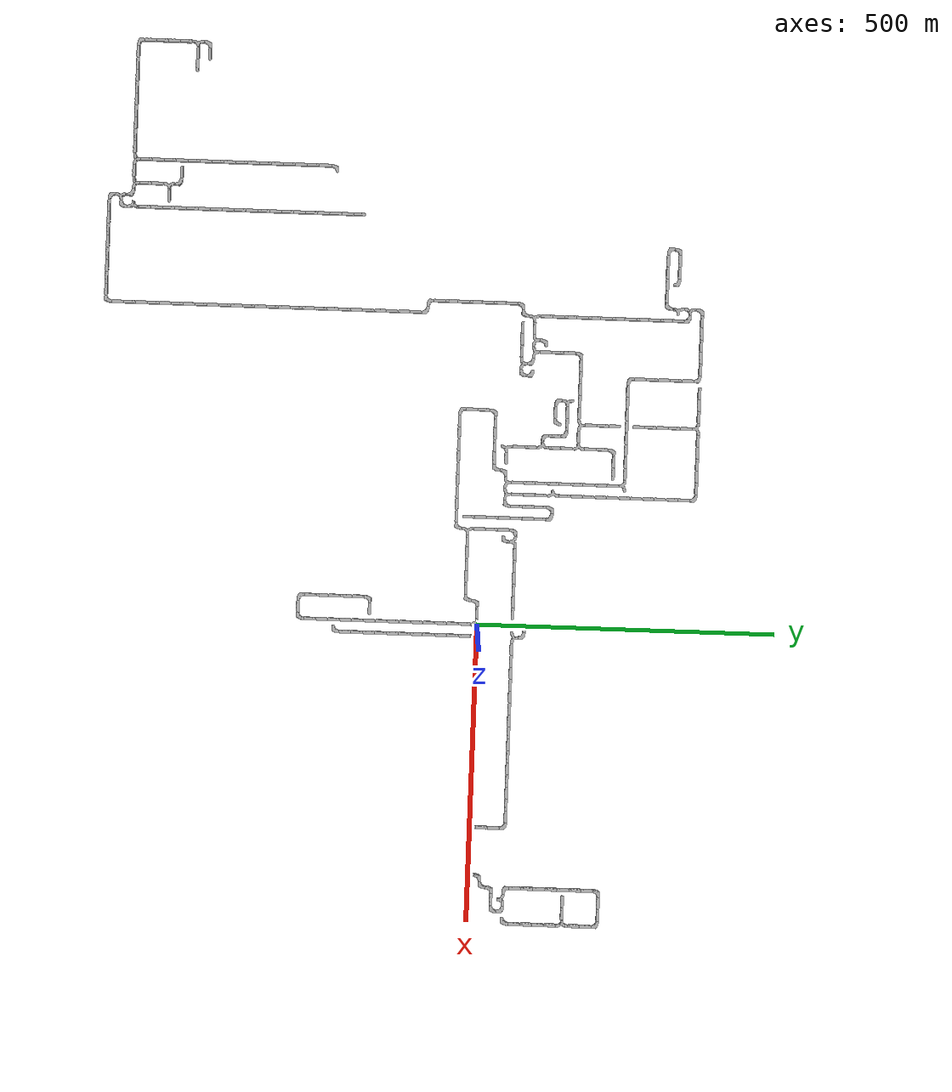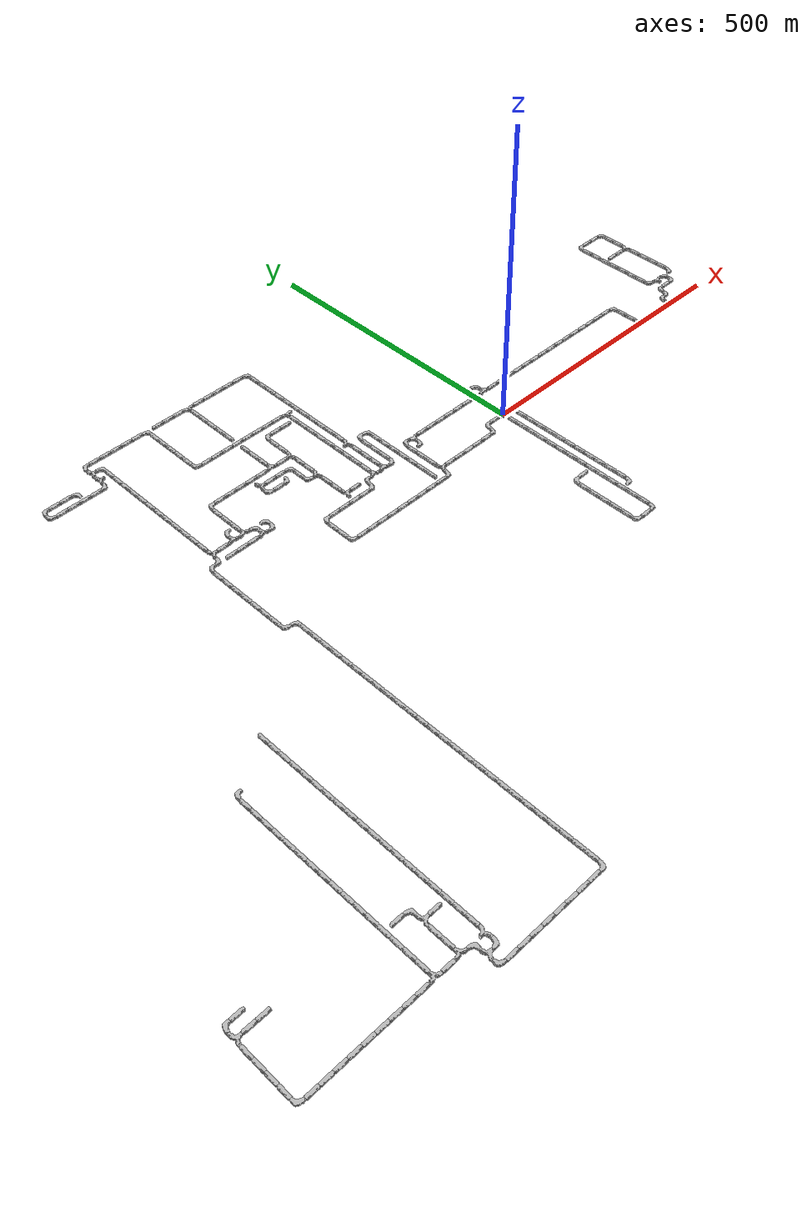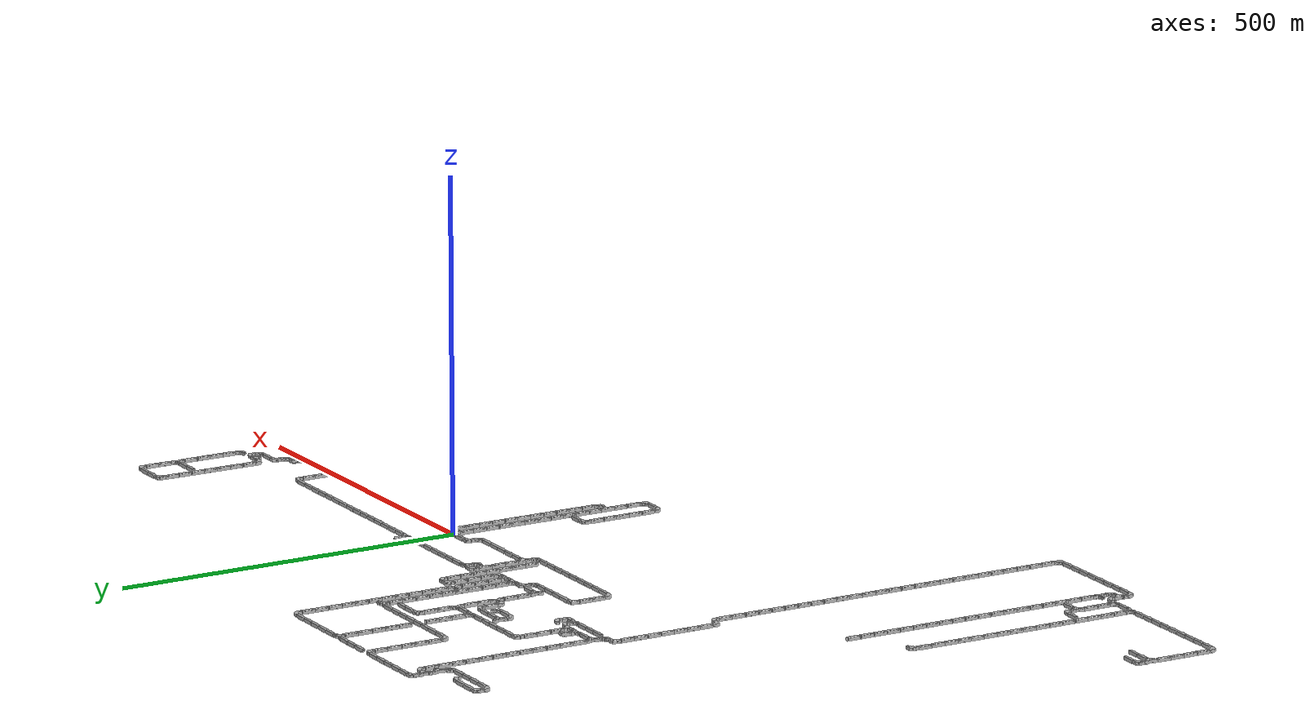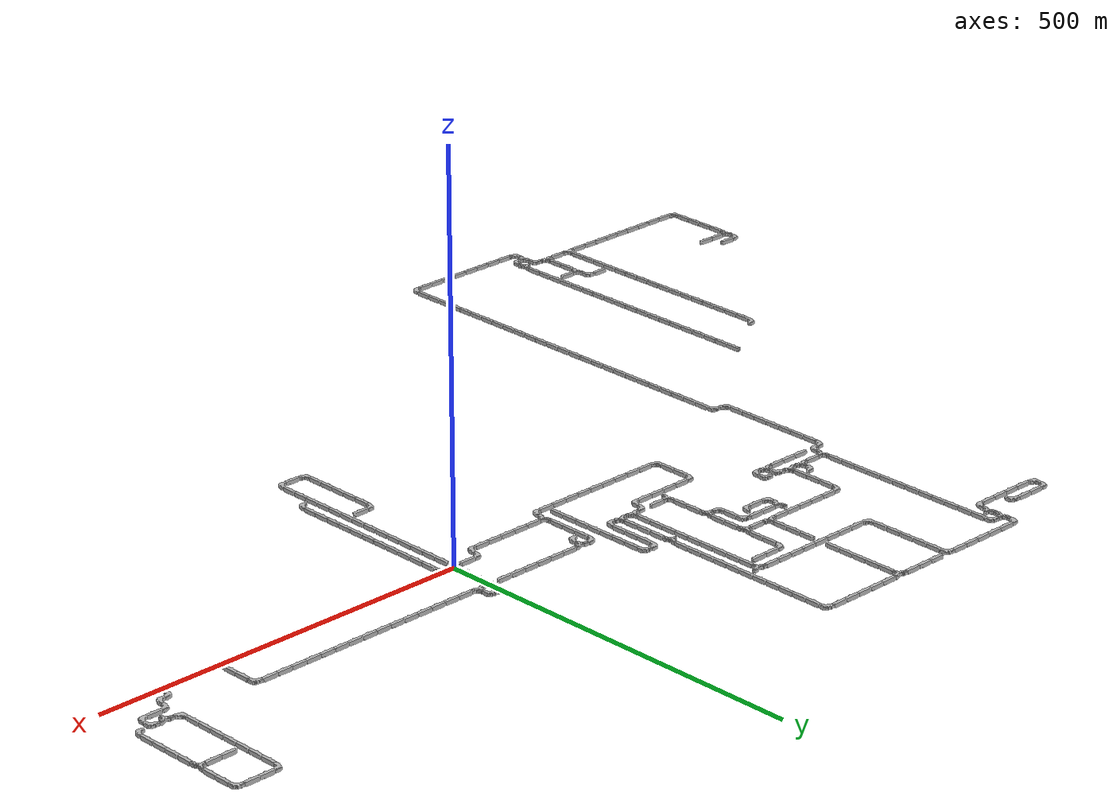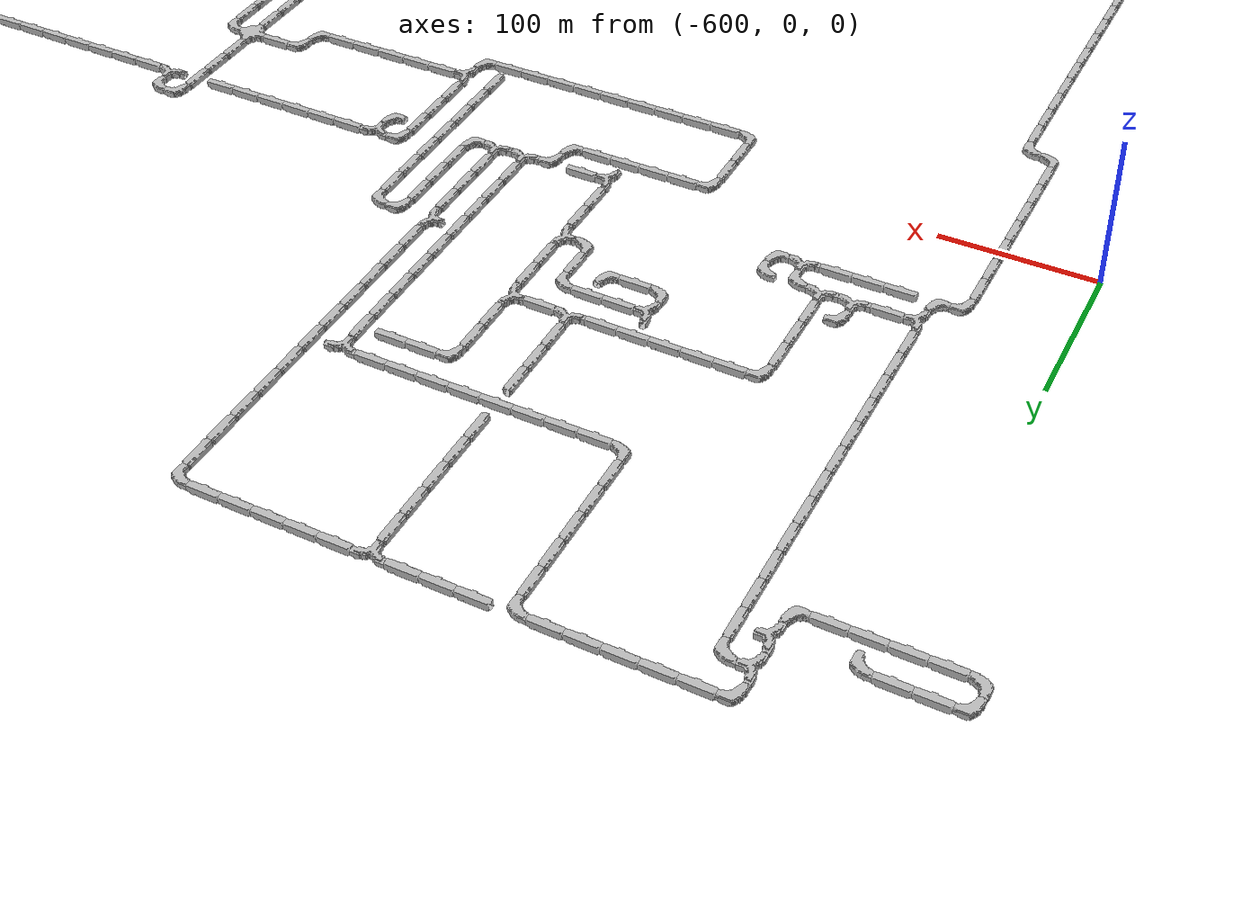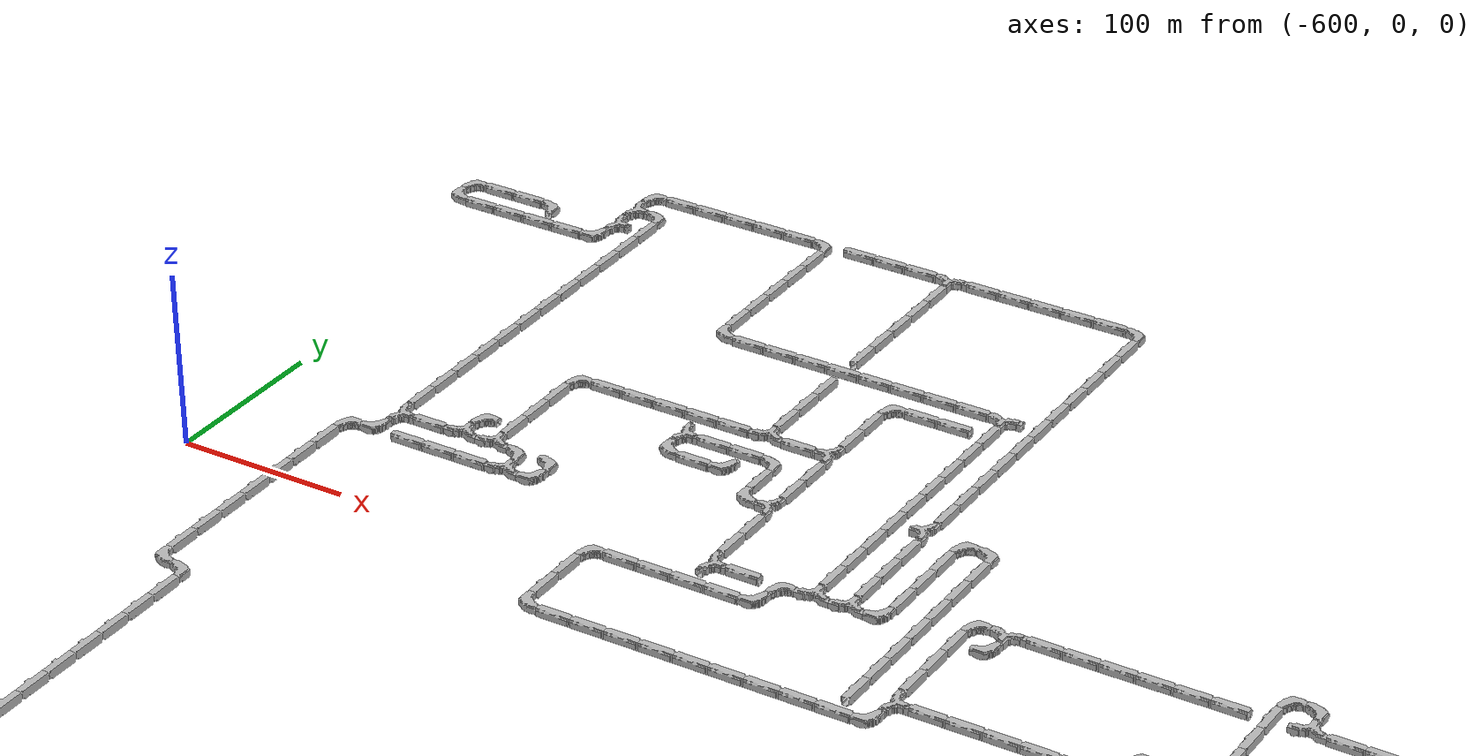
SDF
<sdf version="1.6">
<world name="cave_8000">
<include>
    <static>true</static>
    <name>cave_0_0</name>
    <pose>0 0 0 0 0 -1.5707963267948966</pose>
    <uri>model://cave_4way_20m</uri>
  </include>
  <include>
    <static>true</static>
    <name>cave_1_0</name>
    <pose>20 0 0 0 0 3.141592653589793</pose>
    <uri>model://cave_L_20m</uri>
  </include>
  <include>
    <static>true</static>
    <name>cave_1_-1</name>
    <pose>20 -20 0 0 0 0.0</pose>
    <uri>model://cave_straight_20m</uri>
  </include>
  <include>
    <static>true</static>
    <name>cave_1_-2</name>
    <pose>20 -40 0 0 0 0.0</pose>
    <uri>model://cave_straight_20m</uri>
  </include>
  <include>
    <static>true</static>
    <name>cave_1_-3</name>
    <pose>20 -60 0 0 0 0.0</pose>
    <uri>model://cave_straight_20m</uri>
  </include>
  <include>
    <static>true</static>
    <name>cave_1_-4</name>
    <pose>20 -80 0 0 0 0.0</pose>
    <uri>model://cave_straight_20m</uri>
  </include>
  <include>
    <static>true</static>
    <name>cave_1_-5</name>
    <pose>20 -100 0 0 0 0.0</pose>
    <uri>model://cave_straight_20m</uri>
  </include>
  <include>
    <static>true</static>
    <name>cave_1_-6</name>
    <pose>20 -120 0 0 0 0.0</pose>
    <uri>model://cave_straight_20m</uri>
  </include>
  <include>
    <static>true</static>
    <name>cave_1_-7</name>
    <pose>20 -140 0 0 0 0.0</pose>
    <uri>model://cave_straight_20m</uri>
  </include>
  <include>
    <static>true</static>
    <name>cave_1_-8</name>
    <pose>20 -160 0 0 0 0.0</pose>
    <uri>model://cave_straight_20m</uri>
  </include>
  <include>
    <static>true</static>
    <name>cave_1_-9</name>
    <pose>20 -180 0 0 0 0.0</pose>
    <uri>model://cave_straight_20m</uri>
  </include>
  <include>
    <static>true</static>
    <name>cave_1_-10</name>
    <pose>20 -200 0 0 0 0.0</pose>
    <uri>model://cave_straight_20m</uri>
  </include>
  <include>
    <static>true</static>
    <name>cave_1_-11</name>
    <pose>20 -220 0 0 0 0.0</pose>
    <uri>model://cave_straight_20m</uri>
  </include>
  <include>
    <static>true</static>
    <name>cave_1_-12</name>
    <pose>20 -240 0 0 0 1.5707963267948966</pose>
    <uri>model://cave_L_20m</uri>
  </include>
  <include>
    <static>true</static>
    <name>cave_0_-1</name>
    <pose>0 -20 0 0 0 0.0</pose>
    <uri>model://cave_straight_20m</uri>
  </include>
  <include>
    <static>true</static>
    <name>cave_0_-2</name>
    <pose>0 -40 0 0 0 0.0</pose>
    <uri>model://cave_straight_20m</uri>
  </include>
  <include>
    <static>true</static>
    <name>cave_0_-3</name>
    <pose>0 -60 0 0 0 0.0</pose>
    <uri>model://cave_straight_20m</uri>
  </include>
  <include>
    <static>true</static>
    <name>cave_0_-4</name>
    <pose>0 -80 0 0 0 0.0</pose>
    <uri>model://cave_straight_20m</uri>
  </include>
  <include>
    <static>true</static>
    <name>cave_0_-5</name>
    <pose>0 -100 0 0 0 0.0</pose>
    <uri>model://cave_straight_20m</uri>
  </include>
  <include>
    <static>true</static>
    <name>cave_0_-6</name>
    <pose>0 -120 0 0 0 0.0</pose>
    <uri>model://cave_straight_20m</uri>
  </include>
  <include>
    <static>true</static>
    <name>cave_0_-7</name>
    <pose>0 -140 0 0 0 0.0</pose>
    <uri>model://cave_straight_20m</uri>
  </include>
  <include>
    <static>true</static>
    <name>cave_0_-8</name>
    <pose>0 -160 0 0 0 0.0</pose>
    <uri>model://cave_straight_20m</uri>
  </include>
  <include>
    <static>true</static>
    <name>cave_0_-9</name>
    <pose>0 -180 0 0 0 0.0</pose>
    <uri>model://cave_straight_20m</uri>
  </include>
  <include>
    <static>true</static>
    <name>cave_0_-10</name>
    <pose>0 -200 0 0 0 0.0</pose>
    <uri>model://cave_straight_20m</uri>
  </include>
  <include>
    <static>true</static>
    <name>cave_0_-11</name>
    <pose>0 -220 0 0 0 0.0</pose>
    <uri>model://cave_straight_20m</uri>
  </include>
  <include>
    <static>true</static>
    <name>cave_0_-12</name>
    <pose>0 -240 0 0 0 0.0</pose>
    <uri>model://cave_straight_20m</uri>
  </include>
  <include>
    <static>true</static>
    <name>cave_0_-13</name>
    <pose>0 -260 0 0 0 0.0</pose>
    <uri>model://cave_straight_20m</uri>
  </include>
  <include>
    <static>true</static>
    <name>cave_0_-14</name>
    <pose>0 -280 0 0 0 0.0</pose>
    <uri>model://cave_straight_20m</uri>
  </include>
  <include>
    <static>true</static>
    <name>cave_0_-15</name>
    <pose>0 -300 0 0 0 1.5707963267948966</pose>
    <uri>model://cave_L_20m</uri>
  </include>
  <include>
    <static>true</static>
    <name>cave_-1_-15</name>
    <pose>-20 -300 0 0 0 1.5707963267948966</pose>
    <uri>model://cave_straight_20m</uri>
  </include>
  <include>
    <static>true</static>
    <name>cave_-2_-15</name>
    <pose>-40 -300 0 0 0 0.0</pose>
    <uri>model://cave_L_20m</uri>
  </include>
  <include>
    <static>true</static>
    <name>cave_-2_-14</name>
    <pose>-40 -280 0 0 0 0.0</pose>
    <uri>model://cave_straight_20m</uri>
  </include>
  <include>
    <static>true</static>
    <name>cave_-2_-13</name>
    <pose>-40 -260 0 0 0 0.0</pose>
    <uri>model://cave_straight_20m</uri>
  </include>
  <include>
    <static>true</static>
    <name>cave_-2_-12</name>
    <pose>-40 -240 0 0 0 0.0</pose>
    <uri>model://cave_straight_20m</uri>
  </include>
  <include>
    <static>true</static>
    <name>cave_-2_-11</name>
    <pose>-40 -220 0 0 0 0.0</pose>
    <uri>model://cave_straight_20m</uri>
  </include>
  <include>
    <static>true</static>
    <name>cave_-2_-10</name>
    <pose>-40 -200 0 0 0 0.0</pose>
    <uri>model://cave_straight_20m</uri>
  </include>
  <include>
    <static>true</static>
    <name>cave_-2_-9</name>
    <pose>-40 -180 0 0 0 -1.5707963267948966</pose>
    <uri>model://cave_L_20m</uri>
  </include>
  <include>
    <static>true</static>
    <name>cave_-1_-9</name>
    <pose>-20 -180 0 0 0 1.5707963267948966</pose>
    <uri>model://cave_straight_20m</uri>
  </include>
  <include>
    <static>true</static>
    <name>cave_-1_0</name>
    <pose>-20 0 0 0 0 1.5707963267948966</pose>
    <uri>model://cave_straight_20m</uri>
  </include>
  <include>
    <static>true</static>
    <name>cave_-2_0</name>
    <pose>-40 0 0 0 0 -1.5707963267948966</pose>
    <uri>model://cave_L_20m</uri>
  </include>
  <include>
    <static>true</static>
    <name>cave_-2_-1</name>
    <pose>-40 -20 0 0 0 1.5707963267948966</pose>
    <uri>model://cave_L_20m</uri>
  </include>
  <include>
    <static>true</static>
    <name>cave_-3_-1</name>
    <pose>-60 -20 0 0 0 1.5707963267948966</pose>
    <uri>model://cave_straight_20m</uri>
  </include>
  <include>
    <static>true</static>
    <name>cave_-4_-1</name>
    <pose>-80 -20 0 0 0 1.5707963267948966</pose>
    <uri>model://cave_straight_20m</uri>
  </include>
  <include>
    <static>true</static>
    <name>cave_-5_-1</name>
    <pose>-100 -20 0 0 0 1.5707963267948966</pose>
    <uri>model://cave_straight_20m</uri>
  </include>
  <include>
    <static>true</static>
    <name>cave_-6_-1</name>
    <pose>-120 -20 0 0 0 1.5707963267948966</pose>
    <uri>model://cave_straight_20m</uri>
  </include>
  <include>
    <static>true</static>
    <name>cave_-7_-1</name>
    <pose>-140 -20 0 0 0 1.5707963267948966</pose>
    <uri>model://cave_straight_20m</uri>
  </include>
  <include>
    <static>true</static>
    <name>cave_-8_-1</name>
    <pose>-160 -20 0 0 0 -1.5707963267948966</pose>
    <uri>model://cave_3way_20m</uri>
  </include>
  <include>
    <static>true</static>
    <name>cave_-8_-2</name>
    <pose>-160 -40 0 0 0 1.5707963267948966</pose>
    <uri>model://cave_L_20m</uri>
  </include>
  <include>
    <static>true</static>
    <name>cave_-9_-2</name>
    <pose>-180 -40 0 0 0 1.5707963267948966</pose>
    <uri>model://cave_straight_20m</uri>
  </include>
  <include>
    <static>true</static>
    <name>cave_-10_-2</name>
    <pose>-200 -40 0 0 0 1.5707963267948966</pose>
    <uri>model://cave_straight_20m</uri>
  </include>
  <include>
    <static>true</static>
    <name>cave_-11_-2</name>
    <pose>-220 -40 0 0 0 1.5707963267948966</pose>
    <uri>model://cave_straight_20m</uri>
  </include>
  <include>
    <static>true</static>
    <name>cave_-12_-2</name>
    <pose>-240 -40 0 0 0 1.5707963267948966</pose>
    <uri>model://cave_straight_20m</uri>
  </include>
  <include>
    <static>true</static>
    <name>cave_-13_-2</name>
    <pose>-260 -40 0 0 0 1.5707963267948966</pose>
    <uri>model://cave_straight_20m</uri>
  </include>
  <include>
    <static>true</static>
    <name>cave_-14_-2</name>
    <pose>-280 -40 0 0 0 1.5707963267948966</pose>
    <uri>model://cave_straight_20m</uri>
  </include>
  <include>
    <static>true</static>
    <name>cave_-15_-2</name>
    <pose>-300 -40 0 0 0 1.5707963267948966</pose>
    <uri>model://cave_straight_20m</uri>
  </include>
  <include>
    <static>true</static>
    <name>cave_-16_-2</name>
    <pose>-320 -40 0 0 0 1.5707963267948966</pose>
    <uri>model://cave_straight_20m</uri>
  </include>
  <include>
    <static>true</static>
    <name>cave_-17_-2</name>
    <pose>-340 -40 0 0 0 1.5707963267948966</pose>
    <uri>model://cave_straight_20m</uri>
  </include>
  <include>
    <static>true</static>
    <name>cave_-18_-2</name>
    <pose>-360 -40 0 0 0 0.0</pose>
    <uri>model://cave_L_20m</uri>
  </include>
  <include>
    <static>true</static>
    <name>cave_-18_-1</name>
    <pose>-360 -20 0 0 0 0.0</pose>
    <uri>model://cave_straight_20m</uri>
  </include>
  <include>
    <static>true</static>
    <name>cave_-18_0</name>
    <pose>-360 0 0 0 0 0.0</pose>
    <uri>model://cave_straight_20m</uri>
  </include>
  <include>
    <static>true</static>
    <name>cave_-18_1</name>
    <pose>-360 20 0 0 0 -1.5707963267948966</pose>
    <uri>model://cave_L_20m</uri>
  </include>
  <include>
    <static>true</static>
    <name>cave_-17_1</name>
    <pose>-340 20 0 0 0 1.5707963267948966</pose>
    <uri>model://cave_straight_20m</uri>
  </include>
  <include>
    <static>true</static>
    <name>cave_-16_1</name>
    <pose>-320 20 0 0 0 1.5707963267948966</pose>
    <uri>model://cave_straight_20m</uri>
  </include>
  <include>
    <static>true</static>
    <name>cave_-15_1</name>
    <pose>-300 20 0 0 0 1.5707963267948966</pose>
    <uri>model://cave_straight_20m</uri>
  </include>
  <include>
    <static>true</static>
    <name>cave_-14_1</name>
    <pose>-280 20 0 0 0 1.5707963267948966</pose>
    <uri>model://cave_straight_20m</uri>
  </include>
  <include>
    <static>true</static>
    <name>cave_-13_1</name>
    <pose>-260 20 0 0 0 1.5707963267948966</pose>
    <uri>model://cave_L_20m</uri>
  </include>
  <include>
    <static>true</static>
    <name>cave_-13_2</name>
    <pose>-260 40 0 0 0 -1.5707963267948966</pose>
    <uri>model://cave_L_20m</uri>
  </include>
  <include>
    <static>true</static>
    <name>cave_-12_2</name>
    <pose>-240 40 0 0 0 0.0</pose>
    <uri>model://cave_3way_20m</uri>
  </include>
  <include>
    <static>true</static>
    <name>cave_-11_2</name>
    <pose>-220 40 0 0 0 0.0</pose>
    <uri>model://cave_3way_20m</uri>
  </include>
  <include>
    <static>true</static>
    <name>cave_-10_2</name>
    <pose>-200 40 0 0 0 1.5707963267948966</pose>
    <uri>model://cave_L_20m</uri>
  </include>
  <include>
    <static>true</static>
    <name>cave_-10_3</name>
    <pose>-200 60 0 0 0 0.0</pose>
    <uri>model://cave_straight_20m</uri>
  </include>
  <include>
    <static>true</static>
    <name>cave_-10_4</name>
    <pose>-200 80 0 0 0 0.0</pose>
    <uri>model://cave_straight_20m</uri>
  </include>
  <include>
    <static>true</static>
    <name>cave_-10_5</name>
    <pose>-200 100 0 0 0 0.0</pose>
    <uri>model://cave_straight_20m</uri>
  </include>
  <include>
    <static>true</static>
    <name>cave_-10_6</name>
    <pose>-200 120 0 0 0 -1.5707963267948966</pose>
    <uri>model://cave_L_20m</uri>
  </include>
  <include>
    <static>true</static>
    <name>cave_-9_6</name>
    <pose>-180 120 0 0 0 3.141592653589793</pose>
    <uri>model://cave_L_20m</uri>
  </include>
  <include>
    <static>true</static>
    <name>cave_-9_5</name>
    <pose>-180 100 0 0 0 0.0</pose>
    <uri>model://cave_straight_20m</uri>
  </include>
  <include>
    <static>true</static>
    <name>cave_-9_4</name>
    <pose>-180 80 0 0 0 0.0</pose>
    <uri>model://cave_straight_20m</uri>
  </include>
  <include>
    <static>true</static>
    <name>cave_-9_3</name>
    <pose>-180 60 0 0 0 0.0</pose>
    <uri>model://cave_straight_20m</uri>
  </include>
  <include>
    <static>true</static>
    <name>cave_-9_2</name>
    <pose>-180 40 0 0 0 0.0</pose>
    <uri>model://cave_straight_20m</uri>
  </include>
  <include>
    <static>true</static>
    <name>cave_-9_1</name>
    <pose>-180 20 0 0 0 0.0</pose>
    <uri>model://cave_straight_20m</uri>
  </include>
  <include>
    <static>true</static>
    <name>cave_-9_0</name>
    <pose>-180 0 0 0 0 0.0</pose>
    <uri>model://cave_straight_20m</uri>
  </include>
  <include>
    <static>true</static>
    <name>cave_-9_-1</name>
    <pose>-180 -20 0 0 0 0.0</pose>
    <uri>model://cave_straight_20m</uri>
  </include>
  <include>
    <static>true</static>
    <name>cave_-11_3</name>
    <pose>-220 60 0 0 0 0.0</pose>
    <uri>model://cave_straight_20m</uri>
  </include>
  <include>
    <static>true</static>
    <name>cave_-11_4</name>
    <pose>-220 80 0 0 0 0.0</pose>
    <uri>model://cave_straight_20m</uri>
  </include>
  <include>
    <static>true</static>
    <name>cave_-11_5</name>
    <pose>-220 100 0 0 0 0.0</pose>
    <uri>model://cave_straight_20m</uri>
  </include>
  <include>
    <static>true</static>
    <name>cave_-11_6</name>
    <pose>-220 120 0 0 0 1.5707963267948966</pose>
    <uri>model://cave_3way_20m</uri>
  </include>
  <include>
    <static>true</static>
    <name>cave_-11_7</name>
    <pose>-220 140 0 0 0 0.0</pose>
    <uri>model://cave_straight_20m</uri>
  </include>
  <include>
    <static>true</static>
    <name>cave_-11_8</name>
    <pose>-220 160 0 0 0 0.0</pose>
    <uri>model://cave_straight_20m</uri>
  </include>
  <include>
    <static>true</static>
    <name>cave_-11_9</name>
    <pose>-220 180 0 0 0 0.0</pose>
    <uri>model://cave_straight_20m</uri>
  </include>
  <include>
    <static>true</static>
    <name>cave_-11_10</name>
    <pose>-220 200 0 0 0 0.0</pose>
    <uri>model://cave_straight_20m</uri>
  </include>
  <include>
    <static>true</static>
    <name>cave_-11_11</name>
    <pose>-220 220 0 0 0 0.0</pose>
    <uri>model://cave_straight_20m</uri>
  </include>
  <include>
    <static>true</static>
    <name>cave_-11_12</name>
    <pose>-220 240 0 0 0 0.0</pose>
    <uri>model://cave_straight_20m</uri>
  </include>
  <include>
    <static>true</static>
    <name>cave_-11_13</name>
    <pose>-220 260 0 0 0 0.0</pose>
    <uri>model://cave_straight_20m</uri>
  </include>
  <include>
    <static>true</static>
    <name>cave_-11_14</name>
    <pose>-220 280 0 0 0 0.0</pose>
    <uri>model://cave_straight_20m</uri>
  </include>
  <include>
    <static>true</static>
    <name>cave_-11_15</name>
    <pose>-220 300 0 0 0 0.0</pose>
    <uri>model://cave_straight_20m</uri>
  </include>
  <include>
    <static>true</static>
    <name>cave_-11_16</name>
    <pose>-220 320 0 0 0 0.0</pose>
    <uri>model://cave_straight_20m</uri>
  </include>
  <include>
    <static>true</static>
    <name>cave_-11_17</name>
    <pose>-220 340 0 0 0 0.0</pose>
    <uri>model://cave_straight_20m</uri>
  </include>
  <include>
    <static>true</static>
    <name>cave_-11_18</name>
    <pose>-220 360 0 0 0 3.141592653589793</pose>
    <uri>model://cave_L_20m</uri>
  </include>
  <include>
    <static>true</static>
    <name>cave_-12_18</name>
    <pose>-240 360 0 0 0 1.5707963267948966</pose>
    <uri>model://cave_straight_20m</uri>
  </include>
  <include>
    <static>true</static>
    <name>cave_-13_18</name>
    <pose>-260 360 0 0 0 1.5707963267948966</pose>
    <uri>model://cave_straight_20m</uri>
  </include>
  <include>
    <static>true</static>
    <name>cave_-14_18</name>
    <pose>-280 360 0 0 0 1.5707963267948966</pose>
    <uri>model://cave_straight_20m</uri>
  </include>
  <include>
    <static>true</static>
    <name>cave_-15_18</name>
    <pose>-300 360 0 0 0 1.5707963267948966</pose>
    <uri>model://cave_straight_20m</uri>
  </include>
  <include>
    <static>true</static>
    <name>cave_-16_18</name>
    <pose>-320 360 0 0 0 1.5707963267948966</pose>
    <uri>model://cave_straight_20m</uri>
  </include>
  <include>
    <static>true</static>
    <name>cave_-17_18</name>
    <pose>-340 360 0 0 0 3.141592653589793</pose>
    <uri>model://cave_3way_20m</uri>
  </include>
  <include>
    <static>true</static>
    <name>cave_-17_17</name>
    <pose>-340 340 0 0 0 0.0</pose>
    <uri>model://cave_straight_20m</uri>
  </include>
  <include>
    <static>true</static>
    <name>cave_-17_16</name>
    <pose>-340 320 0 0 0 0.0</pose>
    <uri>model://cave_straight_20m</uri>
  </include>
  <include>
    <static>true</static>
    <name>cave_-17_15</name>
    <pose>-340 300 0 0 0 0.0</pose>
    <uri>model://cave_straight_20m</uri>
  </include>
  <include>
    <static>true</static>
    <name>cave_-17_14</name>
    <pose>-340 280 0 0 0 0.0</pose>
    <uri>model://cave_straight_20m</uri>
  </include>
  <include>
    <static>true</static>
    <name>cave_-17_13</name>
    <pose>-340 260 0 0 0 0.0</pose>
    <uri>model://cave_straight_20m</uri>
  </include>
  <include>
    <static>true</static>
    <name>cave_-18_18</name>
    <pose>-360 360 0 0 0 1.5707963267948966</pose>
    <uri>model://cave_straight_20m</uri>
  </include>
  <include>
    <static>true</static>
    <name>cave_-19_18</name>
    <pose>-380 360 0 0 0 1.5707963267948966</pose>
    <uri>model://cave_straight_20m</uri>
  </include>
  <include>
    <static>true</static>
    <name>cave_-20_18</name>
    <pose>-400 360 0 0 0 1.5707963267948966</pose>
    <uri>model://cave_straight_20m</uri>
  </include>
  <include>
    <static>true</static>
    <name>cave_-12_3</name>
    <pose>-240 60 0 0 0 0.0</pose>
    <uri>model://cave_straight_20m</uri>
  </include>
  <include>
    <static>true</static>
    <name>cave_-12_4</name>
    <pose>-240 80 0 0 0 0.0</pose>
    <uri>model://cave_straight_20m</uri>
  </include>
  <include>
    <static>true</static>
    <name>cave_-12_5</name>
    <pose>-240 100 0 0 0 0.0</pose>
    <uri>model://cave_straight_20m</uri>
  </include>
  <include>
    <static>true</static>
    <name>cave_-12_6</name>
    <pose>-240 120 0 0 0 0.0</pose>
    <uri>model://cave_straight_20m</uri>
  </include>
  <include>
    <static>true</static>
    <name>cave_-12_7</name>
    <pose>-240 140 0 0 0 0.0</pose>
    <uri>model://cave_straight_20m</uri>
  </include>
  <include>
    <static>true</static>
    <name>cave_-12_8</name>
    <pose>-240 160 0 0 0 0.0</pose>
    <uri>model://cave_straight_20m</uri>
  </include>
  <include>
    <static>true</static>
    <name>cave_-12_9</name>
    <pose>-240 180 0 0 0 0.0</pose>
    <uri>model://cave_straight_20m</uri>
  </include>
  <include>
    <static>true</static>
    <name>cave_-12_10</name>
    <pose>-240 200 0 0 0 0.0</pose>
    <uri>model://cave_straight_20m</uri>
  </include>
  <include>
    <static>true</static>
    <name>cave_-12_11</name>
    <pose>-240 220 0 0 0 0.0</pose>
    <uri>model://cave_straight_20m</uri>
  </include>
  <include>
    <static>true</static>
    <name>cave_-12_12</name>
    <pose>-240 240 0 0 0 3.141592653589793</pose>
    <uri>model://cave_3way_20m</uri>
  </include>
  <include>
    <static>true</static>
    <name>cave_-13_12</name>
    <pose>-260 240 0 0 0 1.5707963267948966</pose>
    <uri>model://cave_straight_20m</uri>
  </include>
  <include>
    <static>true</static>
    <name>cave_-14_12</name>
    <pose>-280 240 0 0 0 1.5707963267948966</pose>
    <uri>model://cave_straight_20m</uri>
  </include>
  <include>
    <static>true</static>
    <name>cave_-15_12</name>
    <pose>-300 240 0 0 0 1.5707963267948966</pose>
    <uri>model://cave_straight_20m</uri>
  </include>
  <include>
    <static>true</static>
    <name>cave_-16_12</name>
    <pose>-320 240 0 0 0 1.5707963267948966</pose>
    <uri>model://cave_straight_20m</uri>
  </include>
  <include>
    <static>true</static>
    <name>cave_-17_12</name>
    <pose>-340 240 0 0 0 1.5707963267948966</pose>
    <uri>model://cave_straight_20m</uri>
  </include>
  <include>
    <static>true</static>
    <name>cave_-18_12</name>
    <pose>-360 240 0 0 0 1.5707963267948966</pose>
    <uri>model://cave_straight_20m</uri>
  </include>
  <include>
    <static>true</static>
    <name>cave_-19_12</name>
    <pose>-380 240 0 0 0 1.5707963267948966</pose>
    <uri>model://cave_straight_20m</uri>
  </include>
  <include>
    <static>true</static>
    <name>cave_-20_12</name>
    <pose>-400 240 0 0 0 1.5707963267948966</pose>
    <uri>model://cave_straight_20m</uri>
  </include>
  <include>
    <static>true</static>
    <name>cave_-21_12</name>
    <pose>-420 240 0 0 0 0.0</pose>
    <uri>model://cave_L_20m</uri>
  </include>
  <include>
    <static>true</static>
    <name>cave_-21_13</name>
    <pose>-420 260 0 0 0 0.0</pose>
    <uri>model://cave_straight_20m</uri>
  </include>
  <include>
    <static>true</static>
    <name>cave_-21_14</name>
    <pose>-420 280 0 0 0 0.0</pose>
    <uri>model://cave_straight_20m</uri>
  </include>
  <include>
    <static>true</static>
    <name>cave_-21_15</name>
    <pose>-420 300 0 0 0 0.0</pose>
    <uri>model://cave_straight_20m</uri>
  </include>
  <include>
    <static>true</static>
    <name>cave_-21_16</name>
    <pose>-420 320 0 0 0 0.0</pose>
    <uri>model://cave_straight_20m</uri>
  </include>
  <include>
    <static>true</static>
    <name>cave_-21_17</name>
    <pose>-420 340 0 0 0 0.0</pose>
    <uri>model://cave_straight_20m</uri>
  </include>
  <include>
    <static>true</static>
    <name>cave_-21_18</name>
    <pose>-420 360 0 0 0 3.141592653589793</pose>
    <uri>model://cave_L_20m</uri>
  </include>
  <include>
    <static>true</static>
    <name>cave_-22_18</name>
    <pose>-440 360 0 0 0 1.5707963267948966</pose>
    <uri>model://cave_straight_20m</uri>
  </include>
  <include>
    <static>true</static>
    <name>cave_-23_18</name>
    <pose>-460 360 0 0 0 1.5707963267948966</pose>
    <uri>model://cave_straight_20m</uri>
  </include>
  <include>
    <static>true</static>
    <name>cave_-24_18</name>
    <pose>-480 360 0 0 0 1.5707963267948966</pose>
    <uri>model://cave_straight_20m</uri>
  </include>
  <include>
    <static>true</static>
    <name>cave_-25_18</name>
    <pose>-500 360 0 0 0 1.5707963267948966</pose>
    <uri>model://cave_straight_20m</uri>
  </include>
  <include>
    <static>true</static>
    <name>cave_-26_18</name>
    <pose>-520 360 0 0 0 1.5707963267948966</pose>
    <uri>model://cave_straight_20m</uri>
  </include>
  <include>
    <static>true</static>
    <name>cave_-27_18</name>
    <pose>-540 360 0 0 0 -1.5707963267948966</pose>
    <uri>model://cave_L_20m</uri>
  </include>
  <include>
    <static>true</static>
    <name>cave_-27_17</name>
    <pose>-540 340 0 0 0 -1.5707963267948966</pose>
    <uri>model://cave_3way_20m</uri>
  </include>
  <include>
    <static>true</static>
    <name>cave_-26_17</name>
    <pose>-520 340 0 0 0 3.141592653589793</pose>
    <uri>model://cave_L_20m</uri>
  </include>
  <include>
    <static>true</static>
    <name>cave_-26_16</name>
    <pose>-520 320 0 0 0 0.0</pose>
    <uri>model://cave_straight_20m</uri>
  </include>
  <include>
    <static>true</static>
    <name>cave_-26_15</name>
    <pose>-520 300 0 0 0 0.0</pose>
    <uri>model://cave_straight_20m</uri>
  </include>
  <include>
    <static>true</static>
    <name>cave_-26_14</name>
    <pose>-520 280 0 0 0 0.0</pose>
    <uri>model://cave_straight_20m</uri>
  </include>
  <include>
    <static>true</static>
    <name>cave_-26_13</name>
    <pose>-520 260 0 0 0 0.0</pose>
    <uri>model://cave_straight_20m</uri>
  </include>
  <include>
    <static>true</static>
    <name>cave_-26_12</name>
    <pose>-520 240 0 0 0 0.0</pose>
    <uri>model://cave_straight_20m</uri>
  </include>
  <include>
    <static>true</static>
    <name>cave_-26_11</name>
    <pose>-520 220 0 0 0 0.0</pose>
    <uri>model://cave_straight_20m</uri>
  </include>
  <include>
    <static>true</static>
    <name>cave_-26_10</name>
    <pose>-520 200 0 0 0 0.0</pose>
    <uri>model://cave_straight_20m</uri>
  </include>
  <include>
    <static>true</static>
    <name>cave_-26_9</name>
    <pose>-520 180 0 0 0 0.0</pose>
    <uri>model://cave_straight_20m</uri>
  </include>
  <include>
    <static>true</static>
    <name>cave_-26_8</name>
    <pose>-520 160 0 0 0 0.0</pose>
    <uri>model://cave_straight_20m</uri>
  </include>
  <include>
    <static>true</static>
    <name>cave_-26_7</name>
    <pose>-520 140 0 0 0 0.0</pose>
    <uri>model://cave_straight_20m</uri>
  </include>
  <include>
    <static>true</static>
    <name>cave_-26_6</name>
    <pose>-520 120 0 0 0 0.0</pose>
    <uri>model://cave_straight_20m</uri>
  </include>
  <include>
    <static>true</static>
    <name>cave_-26_5</name>
    <pose>-520 100 0 0 0 0.0</pose>
    <uri>model://cave_straight_20m</uri>
  </include>
  <include>
    <static>true</static>
    <name>cave_-26_4</name>
    <pose>-520 80 0 0 0 -1.5707963267948966</pose>
    <uri>model://cave_3way_20m</uri>
  </include>
  <include>
    <static>true</static>
    <name>cave_-25_4</name>
    <pose>-500 80 0 0 0 1.5707963267948966</pose>
    <uri>model://cave_straight_20m</uri>
  </include>
  <include>
    <static>true</static>
    <name>cave_-24_4</name>
    <pose>-480 80 0 0 0 0.0</pose>
    <uri>model://cave_3way_20m</uri>
  </include>
  <include>
    <static>true</static>
    <name>cave_-23_4</name>
    <pose>-460 80 0 0 0 0.0</pose>
    <uri>model://cave_3way_20m</uri>
  </include>
  <include>
    <static>true</static>
    <name>cave_-22_4</name>
    <pose>-440 80 0 0 0 3.141592653589793</pose>
    <uri>model://cave_L_20m</uri>
  </include>
  <include>
    <static>true</static>
    <name>cave_-22_3</name>
    <pose>-440 60 0 0 0 0.0</pose>
    <uri>model://cave_3way_20m</uri>
  </include>
  <include>
    <static>true</static>
    <name>cave_-21_3</name>
    <pose>-420 60 0 0 0 1.5707963267948966</pose>
    <uri>model://cave_L_20m</uri>
  </include>
  <include>
    <static>true</static>
    <name>cave_-21_4</name>
    <pose>-420 80 0 0 0 3.141592653589793</pose>
    <uri>model://cave_L_20m</uri>
  </include>
  <include>
    <static>true</static>
    <name>cave_-23_3</name>
    <pose>-460 60 0 0 0 1.5707963267948966</pose>
    <uri>model://cave_straight_20m</uri>
  </include>
  <include>
    <static>true</static>
    <name>cave_-24_3</name>
    <pose>-480 60 0 0 0 1.5707963267948966</pose>
    <uri>model://cave_straight_20m</uri>
  </include>
  <include>
    <static>true</static>
    <name>cave_-25_3</name>
    <pose>-500 60 0 0 0 1.5707963267948966</pose>
    <uri>model://cave_straight_20m</uri>
  </include>
  <include>
    <static>true</static>
    <name>cave_-23_5</name>
    <pose>-460 100 0 0 0 0.0</pose>
    <uri>model://cave_straight_20m</uri>
  </include>
  <include>
    <static>true</static>
    <name>cave_-23_6</name>
    <pose>-460 120 0 0 0 0.0</pose>
    <uri>model://cave_straight_20m</uri>
  </include>
  <include>
    <static>true</static>
    <name>cave_-23_7</name>
    <pose>-460 140 0 0 0 0.0</pose>
    <uri>model://cave_straight_20m</uri>
  </include>
  <include>
    <static>true</static>
    <name>cave_-23_8</name>
    <pose>-460 160 0 0 0 -1.5707963267948966</pose>
    <uri>model://cave_L_20m</uri>
  </include>
  <include>
    <static>true</static>
    <name>cave_-22_8</name>
    <pose>-440 160 0 0 0 1.5707963267948966</pose>
    <uri>model://cave_straight_20m</uri>
  </include>
  <include>
    <static>true</static>
    <name>cave_-21_8</name>
    <pose>-420 160 0 0 0 1.5707963267948966</pose>
    <uri>model://cave_straight_20m</uri>
  </include>
  <include>
    <static>true</static>
    <name>cave_-20_8</name>
    <pose>-400 160 0 0 0 1.5707963267948966</pose>
    <uri>model://cave_straight_20m</uri>
  </include>
  <include>
    <static>true</static>
    <name>cave_-19_8</name>
    <pose>-380 160 0 0 0 1.5707963267948966</pose>
    <uri>model://cave_straight_20m</uri>
  </include>
  <include>
    <static>true</static>
    <name>cave_-18_8</name>
    <pose>-360 160 0 0 0 1.5707963267948966</pose>
    <uri>model://cave_straight_20m</uri>
  </include>
  <include>
    <static>true</static>
    <name>cave_-17_8</name>
    <pose>-340 160 0 0 0 0.0</pose>
    <uri>model://cave_3way_20m</uri>
  </include>
  <include>
    <static>true</static>
    <name>cave_-16_8</name>
    <pose>-320 160 0 0 0 1.5707963267948966</pose>
    <uri>model://cave_straight_20m</uri>
  </include>
  <include>
    <static>true</static>
    <name>cave_-15_8</name>
    <pose>-300 160 0 0 0 1.5707963267948966</pose>
    <uri>model://cave_3way_20m</uri>
  </include>
  <include>
    <static>true</static>
    <name>cave_-15_7</name>
    <pose>-300 140 0 0 0 0.0</pose>
    <uri>model://cave_straight_20m</uri>
  </include>
  <include>
    <static>true</static>
    <name>cave_-15_6</name>
    <pose>-300 120 0 0 0 0.0</pose>
    <uri>model://cave_straight_20m</uri>
  </include>
  <include>
    <static>true</static>
    <name>cave_-15_5</name>
    <pose>-300 100 0 0 0 1.5707963267948966</pose>
    <uri>model://cave_3way_20m</uri>
  </include>
  <include>
    <static>true</static>
    <name>cave_-15_4</name>
    <pose>-300 80 0 0 0 0.0</pose>
    <uri>model://cave_straight_20m</uri>
  </include>
  <include>
    <static>true</static>
    <name>cave_-15_3</name>
    <pose>-300 60 0 0 0 0.0</pose>
    <uri>model://cave_straight_20m</uri>
  </include>
  <include>
    <static>true</static>
    <name>cave_-15_2</name>
    <pose>-300 40 0 0 0 -1.5707963267948966</pose>
    <uri>model://cave_3way_20m</uri>
  </include>
  <include>
    <static>true</static>
    <name>cave_-14_2</name>
    <pose>-280 40 0 0 0 1.5707963267948966</pose>
    <uri>model://cave_straight_20m</uri>
  </include>
  <include>
    <static>true</static>
    <name>cave_-16_5</name>
    <pose>-320 100 0 0 0 0.0</pose>
    <uri>model://cave_L_20m</uri>
  </include>
  <include>
    <static>true</static>
    <name>cave_-16_6</name>
    <pose>-320 120 0 0 0 0.0</pose>
    <uri>model://cave_straight_20m</uri>
  </include>
  <include>
    <static>true</static>
    <name>cave_-16_7</name>
    <pose>-320 140 0 0 0 3.141592653589793</pose>
    <uri>model://cave_L_20m</uri>
  </include>
  <include>
    <static>true</static>
    <name>cave_-17_7</name>
    <pose>-340 140 0 0 0 1.5707963267948966</pose>
    <uri>model://cave_straight_20m</uri>
  </include>
  <include>
    <static>true</static>
    <name>cave_-18_7</name>
    <pose>-360 140 0 0 0 1.5707963267948966</pose>
    <uri>model://cave_straight_20m</uri>
  </include>
  <include>
    <static>true</static>
    <name>cave_-19_7</name>
    <pose>-380 140 0 0 0 -1.5707963267948966</pose>
    <uri>model://cave_3way_20m</uri>
  </include>
  <include>
    <static>true</static>
    <name>cave_-19_6</name>
    <pose>-380 120 0 0 0 0.0</pose>
    <uri>model://cave_L_20m</uri>
  </include>
  <include>
    <static>true</static>
    <name>cave_-18_6</name>
    <pose>-360 120 0 0 0 1.5707963267948966</pose>
    <uri>model://cave_straight_20m</uri>
  </include>
  <include>
    <static>true</static>
    <name>cave_-17_6</name>
    <pose>-340 120 0 0 0 1.5707963267948966</pose>
    <uri>model://cave_L_20m</uri>
  </include>
  <include>
    <static>true</static>
    <name>cave_-15_9</name>
    <pose>-300 180 0 0 0 0.0</pose>
    <uri>model://cave_straight_20m</uri>
  </include>
  <include>
    <static>true</static>
    <name>cave_-15_10</name>
    <pose>-300 200 0 0 0 0.0</pose>
    <uri>model://cave_straight_20m</uri>
  </include>
  <include>
    <static>true</static>
    <name>cave_-15_11</name>
    <pose>-300 220 0 0 0 -1.5707963267948966</pose>
    <uri>model://cave_L_20m</uri>
  </include>
  <include>
    <static>true</static>
    <name>cave_-14_11</name>
    <pose>-280 220 0 0 0 1.5707963267948966</pose>
    <uri>model://cave_straight_20m</uri>
  </include>
  <include>
    <static>true</static>
    <name>cave_-13_11</name>
    <pose>-260 220 0 0 0 1.5707963267948966</pose>
    <uri>model://cave_straight_20m</uri>
  </include>
  <include>
    <static>true</static>
    <name>cave_-17_9</name>
    <pose>-340 180 0 0 0 0.0</pose>
    <uri>model://cave_straight_20m</uri>
  </include>
  <include>
    <static>true</static>
    <name>cave_-17_10</name>
    <pose>-340 200 0 0 0 0.0</pose>
    <uri>model://cave_straight_20m</uri>
  </include>
  <include>
    <static>true</static>
    <name>cave_-17_11</name>
    <pose>-340 220 0 0 0 0.0</pose>
    <uri>model://cave_straight_20m</uri>
  </include>
  <include>
    <static>true</static>
    <name>cave_-24_5</name>
    <pose>-480 100 0 0 0 -1.5707963267948966</pose>
    <uri>model://cave_L_20m</uri>
  </include>
  <include>
    <static>true</static>
    <name>cave_-26_3</name>
    <pose>-520 60 0 0 0 1.5707963267948966</pose>
    <uri>model://cave_L_20m</uri>
  </include>
  <include>
    <static>true</static>
    <name>cave_-27_3</name>
    <pose>-540 60 0 0 0 -1.5707963267948966</pose>
    <uri>model://cave_L_20m</uri>
  </include>
  <include>
    <static>true</static>
    <name>cave_-27_2</name>
    <pose>-540 40 0 0 0 0.0</pose>
    <uri>model://cave_straight_20m</uri>
  </include>
  <include>
    <static>true</static>
    <name>cave_-27_1</name>
    <pose>-540 20 0 0 0 0.0</pose>
    <uri>model://cave_straight_20m</uri>
  </include>
  <include>
    <static>true</static>
    <name>cave_-27_0</name>
    <pose>-540 0 0 0 0 0.0</pose>
    <uri>model://cave_straight_20m</uri>
  </include>
  <include>
    <static>true</static>
    <name>cave_-27_-1</name>
    <pose>-540 -20 0 0 0 0.0</pose>
    <uri>model://cave_straight_20m</uri>
  </include>
  <include>
    <static>true</static>
    <name>cave_-27_-2</name>
    <pose>-540 -40 0 0 0 0.0</pose>
    <uri>model://cave_straight_20m</uri>
  </include>
  <include>
    <static>true</static>
    <name>cave_-27_-3</name>
    <pose>-540 -60 0 0 0 0.0</pose>
    <uri>model://cave_straight_20m</uri>
  </include>
  <include>
    <static>true</static>
    <name>cave_-27_-4</name>
    <pose>-540 -80 0 0 0 0.0</pose>
    <uri>model://cave_straight_20m</uri>
  </include>
  <include>
    <static>true</static>
    <name>cave_-27_-5</name>
    <pose>-540 -100 0 0 0 0.0</pose>
    <uri>model://cave_L_20m</uri>
  </include>
  <include>
    <static>true</static>
    <name>cave_-26_-5</name>
    <pose>-520 -100 0 0 0 3.141592653589793</pose>
    <uri>model://cave_L_20m</uri>
  </include>
  <include>
    <static>true</static>
    <name>cave_-26_-6</name>
    <pose>-520 -120 0 0 0 0.0</pose>
    <uri>model://cave_straight_20m</uri>
  </include>
  <include>
    <static>true</static>
    <name>cave_-26_-7</name>
    <pose>-520 -140 0 0 0 0.0</pose>
    <uri>model://cave_straight_20m</uri>
  </include>
  <include>
    <static>true</static>
    <name>cave_-26_-8</name>
    <pose>-520 -160 0 0 0 0.0</pose>
    <uri>model://cave_straight_20m</uri>
  </include>
  <include>
    <static>true</static>
    <name>cave_-26_-9</name>
    <pose>-520 -180 0 0 0 0.0</pose>
    <uri>model://cave_straight_20m</uri>
  </include>
  <include>
    <static>true</static>
    <name>cave_-26_-10</name>
    <pose>-520 -200 0 0 0 0.0</pose>
    <uri>model://cave_straight_20m</uri>
  </include>
  <include>
    <static>true</static>
    <name>cave_-26_-11</name>
    <pose>-520 -220 0 0 0 0.0</pose>
    <uri>model://cave_straight_20m</uri>
  </include>
  <include>
    <static>true</static>
    <name>cave_-26_-12</name>
    <pose>-520 -240 0 0 0 0.0</pose>
    <uri>model://cave_straight_20m</uri>
  </include>
  <include>
    <static>true</static>
    <name>cave_-26_-13</name>
    <pose>-520 -260 0 0 0 0.0</pose>
    <uri>model://cave_straight_20m</uri>
  </include>
  <include>
    <static>true</static>
    <name>cave_-26_-14</name>
    <pose>-520 -280 0 0 0 0.0</pose>
    <uri>model://cave_straight_20m</uri>
  </include>
  <include>
    <static>true</static>
    <name>cave_-26_-15</name>
    <pose>-520 -300 0 0 0 0.0</pose>
    <uri>model://cave_straight_20m</uri>
  </include>
  <include>
    <static>true</static>
    <name>cave_-26_-16</name>
    <pose>-520 -320 0 0 0 0.0</pose>
    <uri>model://cave_straight_20m</uri>
  </include>
  <include>
    <static>true</static>
    <name>cave_-26_-17</name>
    <pose>-520 -340 0 0 0 0.0</pose>
    <uri>model://cave_straight_20m</uri>
  </include>
  <include>
    <static>true</static>
    <name>cave_-26_-18</name>
    <pose>-520 -360 0 0 0 0.0</pose>
    <uri>model://cave_straight_20m</uri>
  </include>
  <include>
    <static>true</static>
    <name>cave_-26_-19</name>
    <pose>-520 -380 0 0 0 0.0</pose>
    <uri>model://cave_straight_20m</uri>
  </include>
  <include>
    <static>true</static>
    <name>cave_-26_-20</name>
    <pose>-520 -400 0 0 0 0.0</pose>
    <uri>model://cave_straight_20m</uri>
  </include>
  <include>
    <static>true</static>
    <name>cave_-26_-21</name>
    <pose>-520 -420 0 0 0 0.0</pose>
    <uri>model://cave_straight_20m</uri>
  </include>
  <include>
    <static>true</static>
    <name>cave_-26_-22</name>
    <pose>-520 -440 0 0 0 0.0</pose>
    <uri>model://cave_straight_20m</uri>
  </include>
  <include>
    <static>true</static>
    <name>cave_-26_-23</name>
    <pose>-520 -460 0 0 0 0.0</pose>
    <uri>model://cave_straight_20m</uri>
  </include>
  <include>
    <static>true</static>
    <name>cave_-26_-24</name>
    <pose>-520 -480 0 0 0 0.0</pose>
    <uri>model://cave_straight_20m</uri>
  </include>
  <include>
    <static>true</static>
    <name>cave_-26_-25</name>
    <pose>-520 -500 0 0 0 0.0</pose>
    <uri>model://cave_straight_20m</uri>
  </include>
  <include>
    <static>true</static>
    <name>cave_-26_-26</name>
    <pose>-520 -520 0 0 0 0.0</pose>
    <uri>model://cave_straight_20m</uri>
  </include>
  <include>
    <static>true</static>
    <name>cave_-26_-27</name>
    <pose>-520 -540 0 0 0 0.0</pose>
    <uri>model://cave_straight_20m</uri>
  </include>
  <include>
    <static>true</static>
    <name>cave_-26_-28</name>
    <pose>-520 -560 0 0 0 0.0</pose>
    <uri>model://cave_straight_20m</uri>
  </include>
  <include>
    <static>true</static>
    <name>cave_-26_-29</name>
    <pose>-520 -580 0 0 0 0.0</pose>
    <uri>model://cave_straight_20m</uri>
  </include>
  <include>
    <static>true</static>
    <name>cave_-26_-30</name>
    <pose>-520 -600 0 0 0 0.0</pose>
    <uri>model://cave_straight_20m</uri>
  </include>
  <include>
    <static>true</static>
    <name>cave_-26_-31</name>
    <pose>-520 -620 0 0 0 0.0</pose>
    <uri>model://cave_straight_20m</uri>
  </include>
  <include>
    <static>true</static>
    <name>cave_-26_-32</name>
    <pose>-520 -640 0 0 0 1.5707963267948966</pose>
    <uri>model://cave_L_20m</uri>
  </include>
  <include>
    <static>true</static>
    <name>cave_-27_-32</name>
    <pose>-540 -640 0 0 0 1.5707963267948966</pose>
    <uri>model://cave_straight_20m</uri>
  </include>
  <include>
    <static>true</static>
    <name>cave_-28_-32</name>
    <pose>-560 -640 0 0 0 1.5707963267948966</pose>
    <uri>model://cave_straight_20m</uri>
  </include>
  <include>
    <static>true</static>
    <name>cave_-29_-32</name>
    <pose>-580 -640 0 0 0 1.5707963267948966</pose>
    <uri>model://cave_straight_20m</uri>
  </include>
  <include>
    <static>true</static>
    <name>cave_-30_-32</name>
    <pose>-600 -640 0 0 0 1.5707963267948966</pose>
    <uri>model://cave_straight_20m</uri>
  </include>
  <include>
    <static>true</static>
    <name>cave_-31_-32</name>
    <pose>-620 -640 0 0 0 1.5707963267948966</pose>
    <uri>model://cave_straight_20m</uri>
  </include>
  <include>
    <static>true</static>
    <name>cave_-32_-32</name>
    <pose>-640 -640 0 0 0 1.5707963267948966</pose>
    <uri>model://cave_straight_20m</uri>
  </include>
  <include>
    <static>true</static>
    <name>cave_-33_-32</name>
    <pose>-660 -640 0 0 0 1.5707963267948966</pose>
    <uri>model://cave_straight_20m</uri>
  </include>
  <include>
    <static>true</static>
    <name>cave_-34_-32</name>
    <pose>-680 -640 0 0 0 1.5707963267948966</pose>
    <uri>model://cave_straight_20m</uri>
  </include>
  <include>
    <static>true</static>
    <name>cave_-35_-32</name>
    <pose>-700 -640 0 0 0 0.0</pose>
    <uri>model://cave_L_20m</uri>
  </include>
  <include>
    <static>true</static>
    <name>cave_-35_-31</name>
    <pose>-700 -620 0 0 0 -1.5707963267948966</pose>
    <uri>model://cave_3way_20m</uri>
  </include>
  <include>
    <static>true</static>
    <name>cave_-34_-31</name>
    <pose>-680 -620 0 0 0 1.5707963267948966</pose>
    <uri>model://cave_L_20m</uri>
  </include>
  <include>
    <static>true</static>
    <name>cave_-34_-30</name>
    <pose>-680 -600 0 0 0 1.5707963267948966</pose>
    <uri>model://cave_3way_20m</uri>
  </include>
  <include>
    <static>true</static>
    <name>cave_-34_-29</name>
    <pose>-680 -580 0 0 0 0.0</pose>
    <uri>model://cave_straight_20m</uri>
  </include>
  <include>
    <static>true</static>
    <name>cave_-34_-28</name>
    <pose>-680 -560 0 0 0 0.0</pose>
    <uri>model://cave_straight_20m</uri>
  </include>
  <include>
    <static>true</static>
    <name>cave_-34_-27</name>
    <pose>-680 -540 0 0 0 0.0</pose>
    <uri>model://cave_straight_20m</uri>
  </include>
  <include>
    <static>true</static>
    <name>cave_-34_-26</name>
    <pose>-680 -520 0 0 0 0.0</pose>
    <uri>model://cave_straight_20m</uri>
  </include>
  <include>
    <static>true</static>
    <name>cave_-34_-25</name>
    <pose>-680 -500 0 0 0 0.0</pose>
    <uri>model://cave_straight_20m</uri>
  </include>
  <include>
    <static>true</static>
    <name>cave_-34_-24</name>
    <pose>-680 -480 0 0 0 0.0</pose>
    <uri>model://cave_straight_20m</uri>
  </include>
  <include>
    <static>true</static>
    <name>cave_-34_-23</name>
    <pose>-680 -460 0 0 0 0.0</pose>
    <uri>model://cave_straight_20m</uri>
  </include>
  <include>
    <static>true</static>
    <name>cave_-34_-22</name>
    <pose>-680 -440 0 0 0 0.0</pose>
    <uri>model://cave_straight_20m</uri>
  </include>
  <include>
    <static>true</static>
    <name>cave_-34_-21</name>
    <pose>-680 -420 0 0 0 0.0</pose>
    <uri>model://cave_straight_20m</uri>
  </include>
  <include>
    <static>true</static>
    <name>cave_-34_-20</name>
    <pose>-680 -400 0 0 0 0.0</pose>
    <uri>model://cave_straight_20m</uri>
  </include>
  <include>
    <static>true</static>
    <name>cave_-34_-19</name>
    <pose>-680 -380 0 0 0 0.0</pose>
    <uri>model://cave_straight_20m</uri>
  </include>
  <include>
    <static>true</static>
    <name>cave_-34_-18</name>
    <pose>-680 -360 0 0 0 0.0</pose>
    <uri>model://cave_straight_20m</uri>
  </include>
  <include>
    <static>true</static>
    <name>cave_-34_-17</name>
    <pose>-680 -340 0 0 0 0.0</pose>
    <uri>model://cave_straight_20m</uri>
  </include>
  <include>
    <static>true</static>
    <name>cave_-34_-16</name>
    <pose>-680 -320 0 0 0 0.0</pose>
    <uri>model://cave_straight_20m</uri>
  </include>
  <include>
    <static>true</static>
    <name>cave_-34_-15</name>
    <pose>-680 -300 0 0 0 0.0</pose>
    <uri>model://cave_straight_20m</uri>
  </include>
  <include>
    <static>true</static>
    <name>cave_-34_-14</name>
    <pose>-680 -280 0 0 0 0.0</pose>
    <uri>model://cave_straight_20m</uri>
  </include>
  <include>
    <static>true</static>
    <name>cave_-34_-13</name>
    <pose>-680 -260 0 0 0 0.0</pose>
    <uri>model://cave_straight_20m</uri>
  </include>
  <include>
    <static>true</static>
    <name>cave_-34_-12</name>
    <pose>-680 -240 0 0 0 0.0</pose>
    <uri>model://cave_straight_20m</uri>
  </include>
  <include>
    <static>true</static>
    <name>cave_-34_-11</name>
    <pose>-680 -220 0 0 0 0.0</pose>
    <uri>model://cave_straight_20m</uri>
  </include>
  <include>
    <static>true</static>
    <name>cave_-35_-30</name>
    <pose>-700 -600 0 0 0 3.141592653589793</pose>
    <uri>model://cave_L_20m</uri>
  </include>
  <include>
    <static>true</static>
    <name>cave_-36_-30</name>
    <pose>-720 -600 0 0 0 0.0</pose>
    <uri>model://cave_3way_20m</uri>
  </include>
  <include>
    <static>true</static>
    <name>cave_-37_-30</name>
    <pose>-740 -600 0 0 0 1.5707963267948966</pose>
    <uri>model://cave_straight_20m</uri>
  </include>
  <include>
    <static>true</static>
    <name>cave_-38_-30</name>
    <pose>-760 -600 0 0 0 0.0</pose>
    <uri>model://cave_3way_20m</uri>
  </include>
  <include>
    <static>true</static>
    <name>cave_-39_-30</name>
    <pose>-780 -600 0 0 0 1.5707963267948966</pose>
    <uri>model://cave_straight_20m</uri>
  </include>
  <include>
    <static>true</static>
    <name>cave_-40_-30</name>
    <pose>-800 -600 0 0 0 1.5707963267948966</pose>
    <uri>model://cave_straight_20m</uri>
  </include>
  <include>
    <static>true</static>
    <name>cave_-41_-30</name>
    <pose>-820 -600 0 0 0 1.5707963267948966</pose>
    <uri>model://cave_straight_20m</uri>
  </include>
  <include>
    <static>true</static>
    <name>cave_-42_-30</name>
    <pose>-840 -600 0 0 0 1.5707963267948966</pose>
    <uri>model://cave_straight_20m</uri>
  </include>
  <include>
    <static>true</static>
    <name>cave_-43_-30</name>
    <pose>-860 -600 0 0 0 1.5707963267948966</pose>
    <uri>model://cave_straight_20m</uri>
  </include>
  <include>
    <static>true</static>
    <name>cave_-44_-30</name>
    <pose>-880 -600 0 0 0 1.5707963267948966</pose>
    <uri>model://cave_straight_20m</uri>
  </include>
  <include>
    <static>true</static>
    <name>cave_-45_-30</name>
    <pose>-900 -600 0 0 0 1.5707963267948966</pose>
    <uri>model://cave_straight_20m</uri>
  </include>
  <include>
    <static>true</static>
    <name>cave_-46_-30</name>
    <pose>-920 -600 0 0 0 1.5707963267948966</pose>
    <uri>model://cave_straight_20m</uri>
  </include>
  <include>
    <static>true</static>
    <name>cave_-47_-30</name>
    <pose>-940 -600 0 0 0 1.5707963267948966</pose>
    <uri>model://cave_straight_20m</uri>
  </include>
  <include>
    <static>true</static>
    <name>cave_-48_-30</name>
    <pose>-960 -600 0 0 0 0.0</pose>
    <uri>model://cave_L_20m</uri>
  </include>
  <include>
    <static>true</static>
    <name>cave_-48_-29</name>
    <pose>-960 -580 0 0 0 0.0</pose>
    <uri>model://cave_straight_20m</uri>
  </include>
  <include>
    <static>true</static>
    <name>cave_-48_-28</name>
    <pose>-960 -560 0 0 0 0.0</pose>
    <uri>model://cave_straight_20m</uri>
  </include>
  <include>
    <static>true</static>
    <name>cave_-48_-27</name>
    <pose>-960 -540 0 0 0 0.0</pose>
    <uri>model://cave_straight_20m</uri>
  </include>
  <include>
    <static>true</static>
    <name>cave_-48_-26</name>
    <pose>-960 -520 0 0 0 0.0</pose>
    <uri>model://cave_straight_20m</uri>
  </include>
  <include>
    <static>true</static>
    <name>cave_-48_-25</name>
    <pose>-960 -500 0 0 0 -1.5707963267948966</pose>
    <uri>model://cave_3way_20m</uri>
  </include>
  <include>
    <static>true</static>
    <name>cave_-47_-25</name>
    <pose>-940 -500 0 0 0 1.5707963267948966</pose>
    <uri>model://cave_straight_20m</uri>
  </include>
  <include>
    <static>true</static>
    <name>cave_-46_-25</name>
    <pose>-920 -500 0 0 0 1.5707963267948966</pose>
    <uri>model://cave_straight_20m</uri>
  </include>
  <include>
    <static>true</static>
    <name>cave_-48_-24</name>
    <pose>-960 -480 0 0 0 -1.5707963267948966</pose>
    <uri>model://cave_L_20m</uri>
  </include>
  <include>
    <static>true</static>
    <name>cave_-47_-24</name>
    <pose>-940 -480 0 0 0 1.5707963267948966</pose>
    <uri>model://cave_straight_20m</uri>
  </include>
  <include>
    <static>true</static>
    <name>cave_-38_-29</name>
    <pose>-760 -580 0 0 0 0.0</pose>
    <uri>model://cave_straight_20m</uri>
  </include>
  <include>
    <static>true</static>
    <name>cave_-38_-28</name>
    <pose>-760 -560 0 0 0 0.0</pose>
    <uri>model://cave_straight_20m</uri>
  </include>
  <include>
    <static>true</static>
    <name>cave_-38_-27</name>
    <pose>-760 -540 0 0 0 0.0</pose>
    <uri>model://cave_straight_20m</uri>
  </include>
  <include>
    <static>true</static>
    <name>cave_-38_-26</name>
    <pose>-760 -520 0 0 0 0.0</pose>
    <uri>model://cave_straight_20m</uri>
  </include>
  <include>
    <static>true</static>
    <name>cave_-38_-25</name>
    <pose>-760 -500 0 0 0 0.0</pose>
    <uri>model://cave_straight_20m</uri>
  </include>
  <include>
    <static>true</static>
    <name>cave_-38_-24</name>
    <pose>-760 -480 0 0 0 0.0</pose>
    <uri>model://cave_straight_20m</uri>
  </include>
  <include>
    <static>true</static>
    <name>cave_-38_-23</name>
    <pose>-760 -460 0 0 0 0.0</pose>
    <uri>model://cave_straight_20m</uri>
  </include>
  <include>
    <static>true</static>
    <name>cave_-38_-22</name>
    <pose>-760 -440 0 0 0 0.0</pose>
    <uri>model://cave_straight_20m</uri>
  </include>
  <include>
    <static>true</static>
    <name>cave_-38_-21</name>
    <pose>-760 -420 0 0 0 0.0</pose>
    <uri>model://cave_straight_20m</uri>
  </include>
  <include>
    <static>true</static>
    <name>cave_-38_-20</name>
    <pose>-760 -400 0 0 0 0.0</pose>
    <uri>model://cave_straight_20m</uri>
  </include>
  <include>
    <static>true</static>
    <name>cave_-38_-19</name>
    <pose>-760 -380 0 0 0 0.0</pose>
    <uri>model://cave_straight_20m</uri>
  </include>
  <include>
    <static>true</static>
    <name>cave_-38_-18</name>
    <pose>-760 -360 0 0 0 0.0</pose>
    <uri>model://cave_straight_20m</uri>
  </include>
  <include>
    <static>true</static>
    <name>cave_-38_-17</name>
    <pose>-760 -340 0 0 0 0.0</pose>
    <uri>model://cave_straight_20m</uri>
  </include>
  <include>
    <static>true</static>
    <name>cave_-38_-16</name>
    <pose>-760 -320 0 0 0 0.0</pose>
    <uri>model://cave_straight_20m</uri>
  </include>
  <include>
    <static>true</static>
    <name>cave_-38_-15</name>
    <pose>-760 -300 0 0 0 0.0</pose>
    <uri>model://cave_straight_20m</uri>
  </include>
  <include>
    <static>true</static>
    <name>cave_-38_-14</name>
    <pose>-760 -280 0 0 0 0.0</pose>
    <uri>model://cave_straight_20m</uri>
  </include>
  <include>
    <static>true</static>
    <name>cave_-38_-13</name>
    <pose>-760 -260 0 0 0 -1.5707963267948966</pose>
    <uri>model://cave_L_20m</uri>
  </include>
  <include>
    <static>true</static>
    <name>cave_-36_-29</name>
    <pose>-720 -580 0 0 0 0.0</pose>
    <uri>model://cave_straight_20m</uri>
  </include>
  <include>
    <static>true</static>
    <name>cave_-36_-28</name>
    <pose>-720 -560 0 0 0 0.0</pose>
    <uri>model://cave_straight_20m</uri>
  </include>
  <include>
    <static>true</static>
    <name>cave_-36_-27</name>
    <pose>-720 -540 0 0 0 -1.5707963267948966</pose>
    <uri>model://cave_3way_20m</uri>
  </include>
  <include>
    <static>true</static>
    <name>cave_-35_-27</name>
    <pose>-700 -540 0 0 0 1.5707963267948966</pose>
    <uri>model://cave_straight_20m</uri>
  </include>
  <include>
    <static>true</static>
    <name>cave_-36_-26</name>
    <pose>-720 -520 0 0 0 3.141592653589793</pose>
    <uri>model://cave_L_20m</uri>
  </include>
  <include>
    <static>true</static>
    <name>cave_-37_-26</name>
    <pose>-740 -520 0 0 0 1.5707963267948966</pose>
    <uri>model://cave_straight_20m</uri>
  </include>
  <include>
    <static>true</static>
    <name>cave_-27_16</name>
    <pose>-540 320 0 0 0 -1.5707963267948966</pose>
    <uri>model://cave_3way_20m</uri>
  </include>
  <include>
    <static>true</static>
    <name>cave_-27_15</name>
    <pose>-540 300 0 0 0 1.5707963267948966</pose>
    <uri>model://cave_L_20m</uri>
  </include>
  <include>
    <static>true</static>
    <name>cave_-28_15</name>
    <pose>-560 300 0 0 0 1.5707963267948966</pose>
    <uri>model://cave_straight_20m</uri>
  </include>
  <include>
    <static>true</static>
    <name>cave_-29_15</name>
    <pose>-580 300 0 0 0 1.5707963267948966</pose>
    <uri>model://cave_straight_20m</uri>
  </include>
  <include>
    <static>true</static>
    <name>cave_-30_15</name>
    <pose>-600 300 0 0 0 1.5707963267948966</pose>
    <uri>model://cave_straight_20m</uri>
  </include>
  <include>
    <static>true</static>
    <name>cave_-31_15</name>
    <pose>-620 300 0 0 0 1.5707963267948966</pose>
    <uri>model://cave_straight_20m</uri>
  </include>
  <include>
    <static>true</static>
    <name>cave_-32_15</name>
    <pose>-640 300 0 0 0 0.0</pose>
    <uri>model://cave_L_20m</uri>
  </include>
  <include>
    <static>true</static>
    <name>cave_-32_16</name>
    <pose>-640 320 0 0 0 -1.5707963267948966</pose>
    <uri>model://cave_L_20m</uri>
  </include>
  <include>
    <static>true</static>
    <name>cave_-31_16</name>
    <pose>-620 320 0 0 0 1.5707963267948966</pose>
    <uri>model://cave_straight_20m</uri>
  </include>
  <include>
    <static>true</static>
    <name>cave_-30_16</name>
    <pose>-600 320 0 0 0 1.5707963267948966</pose>
    <uri>model://cave_straight_20m</uri>
  </include>
  <include>
    <static>true</static>
    <name>cave_-29_16</name>
    <pose>-580 320 0 0 0 3.141592653589793</pose>
    <uri>model://cave_L_20m</uri>
  </include>
  <include>
    <static>true</static>
    <name>cave_-8_0</name>
    <pose>-160 0 0 0 0 0.0</pose>
    <uri>model://cave_straight_20m</uri>
  </include>
  <include>
    <static>true</static>
    <name>cave_-8_1</name>
    <pose>-160 20 0 0 0 0.0</pose>
    <uri>model://cave_straight_20m</uri>
  </include>
  <include>
    <static>true</static>
    <name>cave_-8_2</name>
    <pose>-160 40 0 0 0 0.0</pose>
    <uri>model://cave_straight_20m</uri>
  </include>
  <include>
    <static>true</static>
    <name>cave_-8_3</name>
    <pose>-160 60 0 0 0 -1.5707963267948966</pose>
    <uri>model://cave_L_20m</uri>
  </include>
  <include>
    <static>true</static>
    <name>cave_-7_3</name>
    <pose>-140 60 0 0 0 3.141592653589793</pose>
    <uri>model://cave_3way_20m</uri>
  </include>
  <include>
    <static>true</static>
    <name>cave_-6_3</name>
    <pose>-120 60 0 0 0 1.5707963267948966</pose>
    <uri>model://cave_straight_20m</uri>
  </include>
  <include>
    <static>true</static>
    <name>cave_-5_3</name>
    <pose>-100 60 0 0 0 1.5707963267948966</pose>
    <uri>model://cave_straight_20m</uri>
  </include>
  <include>
    <static>true</static>
    <name>cave_-4_3</name>
    <pose>-80 60 0 0 0 1.5707963267948966</pose>
    <uri>model://cave_straight_20m</uri>
  </include>
  <include>
    <static>true</static>
    <name>cave_-3_3</name>
    <pose>-60 60 0 0 0 1.5707963267948966</pose>
    <uri>model://cave_straight_20m</uri>
  </include>
  <include>
    <static>true</static>
    <name>cave_-2_3</name>
    <pose>-40 60 0 0 0 1.5707963267948966</pose>
    <uri>model://cave_straight_20m</uri>
  </include>
  <include>
    <static>true</static>
    <name>cave_-1_3</name>
    <pose>-20 60 0 0 0 1.5707963267948966</pose>
    <uri>model://cave_straight_20m</uri>
  </include>
  <include>
    <static>true</static>
    <name>cave_-7_2</name>
    <pose>-140 40 0 0 0 1.5707963267948966</pose>
    <uri>model://cave_L_20m</uri>
  </include>
  <include>
    <static>true</static>
    <name>cave_0_1</name>
    <pose>0 20 0 0 0 0.0</pose>
    <uri>model://cave_straight_20m</uri>
  </include>
  <include>
    <static>true</static>
    <name>cave_0_2</name>
    <pose>0 40 0 0 0 0.0</pose>
    <uri>model://cave_straight_20m</uri>
  </include>
  <include>
    <static>true</static>
    <name>cave_0_3</name>
    <pose>0 60 0 0 0 0.0</pose>
    <uri>model://cave_straight_20m</uri>
  </include>
  <include>
    <static>true</static>
    <name>cave_0_4</name>
    <pose>0 80 0 0 0 -1.5707963267948966</pose>
    <uri>model://cave_L_20m</uri>
  </include>
  <include>
    <static>true</static>
    <name>cave_1_4</name>
    <pose>20 80 0 0 0 3.141592653589793</pose>
    <uri>model://cave_L_20m</uri>
  </include>
  <include>
    <static>true</static>
    <name>cave_1_3</name>
    <pose>20 60 0 0 0 0.0</pose>
    <uri>model://cave_3way_20m</uri>
  </include>
  <include>
    <static>true</static>
    <name>cave_2_3</name>
    <pose>40 60 0 0 0 1.5707963267948966</pose>
    <uri>model://cave_straight_20m</uri>
  </include>
  <include>
    <static>true</static>
    <name>cave_3_3</name>
    <pose>60 60 0 0 0 1.5707963267948966</pose>
    <uri>model://cave_straight_20m</uri>
  </include>
  <include>
    <static>true</static>
    <name>cave_4_3</name>
    <pose>80 60 0 0 0 1.5707963267948966</pose>
    <uri>model://cave_straight_20m</uri>
  </include>
  <include>
    <static>true</static>
    <name>cave_5_3</name>
    <pose>100 60 0 0 0 1.5707963267948966</pose>
    <uri>model://cave_straight_20m</uri>
  </include>
  <include>
    <static>true</static>
    <name>cave_6_3</name>
    <pose>120 60 0 0 0 1.5707963267948966</pose>
    <uri>model://cave_straight_20m</uri>
  </include>
  <include>
    <static>true</static>
    <name>cave_7_3</name>
    <pose>140 60 0 0 0 1.5707963267948966</pose>
    <uri>model://cave_straight_20m</uri>
  </include>
  <include>
    <static>true</static>
    <name>cave_8_3</name>
    <pose>160 60 0 0 0 1.5707963267948966</pose>
    <uri>model://cave_straight_20m</uri>
  </include>
  <include>
    <static>true</static>
    <name>cave_9_3</name>
    <pose>180 60 0 0 0 1.5707963267948966</pose>
    <uri>model://cave_straight_20m</uri>
  </include>
  <include>
    <static>true</static>
    <name>cave_10_3</name>
    <pose>200 60 0 0 0 1.5707963267948966</pose>
    <uri>model://cave_straight_20m</uri>
  </include>
  <include>
    <static>true</static>
    <name>cave_11_3</name>
    <pose>220 60 0 0 0 1.5707963267948966</pose>
    <uri>model://cave_straight_20m</uri>
  </include>
  <include>
    <static>true</static>
    <name>cave_12_3</name>
    <pose>240 60 0 0 0 1.5707963267948966</pose>
    <uri>model://cave_straight_20m</uri>
  </include>
  <include>
    <static>true</static>
    <name>cave_13_3</name>
    <pose>260 60 0 0 0 1.5707963267948966</pose>
    <uri>model://cave_straight_20m</uri>
  </include>
  <include>
    <static>true</static>
    <name>cave_14_3</name>
    <pose>280 60 0 0 0 1.5707963267948966</pose>
    <uri>model://cave_straight_20m</uri>
  </include>
  <include>
    <static>true</static>
    <name>cave_15_3</name>
    <pose>300 60 0 0 0 1.5707963267948966</pose>
    <uri>model://cave_straight_20m</uri>
  </include>
  <include>
    <static>true</static>
    <name>cave_16_3</name>
    <pose>320 60 0 0 0 1.5707963267948966</pose>
    <uri>model://cave_straight_20m</uri>
  </include>
  <include>
    <static>true</static>
    <name>cave_17_3</name>
    <pose>340 60 0 0 0 3.141592653589793</pose>
    <uri>model://cave_L_20m</uri>
  </include>
  <include>
    <static>true</static>
    <name>cave_17_2</name>
    <pose>340 40 0 0 0 0.0</pose>
    <uri>model://cave_straight_20m</uri>
  </include>
  <include>
    <static>true</static>
    <name>cave_17_1</name>
    <pose>340 20 0 0 0 0.0</pose>
    <uri>model://cave_straight_20m</uri>
  </include>
  <include>
    <static>true</static>
    <name>cave_17_0</name>
    <pose>340 0 0 0 0 0.0</pose>
    <uri>model://cave_L_20m</uri>
  </include>
  <include>
    <static>true</static>
    <name>cave_18_0</name>
    <pose>360 0 0 0 0 1.5707963267948966</pose>
    <uri>model://cave_straight_20m</uri>
  </include>
  <include>
    <static>true</static>
    <name>cave_19_0</name>
    <pose>380 0 0 0 0 1.5707963267948966</pose>
    <uri>model://cave_straight_20m</uri>
  </include>
  <include>
    <static>true</static>
    <name>cave_20_0</name>
    <pose>400 0 0 0 0 1.5707963267948966</pose>
    <uri>model://cave_straight_20m</uri>
  </include>
  <include>
    <static>true</static>
    <name>cave_21_0</name>
    <pose>420 0 0 0 0 1.5707963267948966</pose>
    <uri>model://cave_L_20m</uri>
  </include>
  <include>
    <static>true</static>
    <name>cave_21_1</name>
    <pose>420 20 0 0 0 -1.5707963267948966</pose>
    <uri>model://cave_L_20m</uri>
  </include>
  <include>
    <static>true</static>
    <name>cave_22_1</name>
    <pose>440 20 0 0 0 1.5707963267948966</pose>
    <uri>model://cave_L_20m</uri>
  </include>
  <include>
    <static>true</static>
    <name>cave_22_2</name>
    <pose>440 40 0 0 0 -1.5707963267948966</pose>
    <uri>model://cave_L_20m</uri>
  </include>
  <include>
    <static>true</static>
    <name>cave_23_2</name>
    <pose>460 40 0 0 0 1.5707963267948966</pose>
    <uri>model://cave_straight_20m</uri>
  </include>
  <include>
    <static>true</static>
    <name>cave_24_2</name>
    <pose>480 40 0 0 0 1.5707963267948966</pose>
    <uri>model://cave_L_20m</uri>
  </include>
  <include>
    <static>true</static>
    <name>cave_24_3</name>
    <pose>480 60 0 0 0 3.141592653589793</pose>
    <uri>model://cave_L_20m</uri>
  </include>
  <include>
    <static>true</static>
    <name>cave_23_3</name>
    <pose>460 60 0 0 0 3.141592653589793</pose>
    <uri>model://cave_3way_20m</uri>
  </include>
  <include>
    <static>true</static>
    <name>cave_22_3</name>
    <pose>440 60 0 0 0 0.0</pose>
    <uri>model://cave_L_20m</uri>
  </include>
  <include>
    <static>true</static>
    <name>cave_22_4</name>
    <pose>440 80 0 0 0 0.0</pose>
    <uri>model://cave_straight_20m</uri>
  </include>
  <include>
    <static>true</static>
    <name>cave_22_5</name>
    <pose>440 100 0 0 0 0.0</pose>
    <uri>model://cave_straight_20m</uri>
  </include>
  <include>
    <static>true</static>
    <name>cave_22_6</name>
    <pose>440 120 0 0 0 0.0</pose>
    <uri>model://cave_straight_20m</uri>
  </include>
  <include>
    <static>true</static>
    <name>cave_22_7</name>
    <pose>440 140 0 0 0 0.0</pose>
    <uri>model://cave_straight_20m</uri>
  </include>
  <include>
    <static>true</static>
    <name>cave_22_8</name>
    <pose>440 160 0 0 0 0.0</pose>
    <uri>model://cave_straight_20m</uri>
  </include>
  <include>
    <static>true</static>
    <name>cave_22_9</name>
    <pose>440 180 0 0 0 0.0</pose>
    <uri>model://cave_straight_20m</uri>
  </include>
  <include>
    <static>true</static>
    <name>cave_22_10</name>
    <pose>440 200 0 0 0 0.0</pose>
    <uri>model://cave_straight_20m</uri>
  </include>
  <include>
    <static>true</static>
    <name>cave_22_11</name>
    <pose>440 220 0 0 0 -1.5707963267948966</pose>
    <uri>model://cave_L_20m</uri>
  </include>
  <include>
    <static>true</static>
    <name>cave_23_11</name>
    <pose>460 220 0 0 0 1.5707963267948966</pose>
    <uri>model://cave_straight_20m</uri>
  </include>
  <include>
    <static>true</static>
    <name>cave_24_11</name>
    <pose>480 220 0 0 0 1.5707963267948966</pose>
    <uri>model://cave_straight_20m</uri>
  </include>
  <include>
    <static>true</static>
    <name>cave_25_11</name>
    <pose>500 220 0 0 0 3.141592653589793</pose>
    <uri>model://cave_L_20m</uri>
  </include>
  <include>
    <static>true</static>
    <name>cave_25_10</name>
    <pose>500 200 0 0 0 0.0</pose>
    <uri>model://cave_straight_20m</uri>
  </include>
  <include>
    <static>true</static>
    <name>cave_25_9</name>
    <pose>500 180 0 0 0 0.0</pose>
    <uri>model://cave_straight_20m</uri>
  </include>
  <include>
    <static>true</static>
    <name>cave_25_8</name>
    <pose>500 160 0 0 0 1.5707963267948966</pose>
    <uri>model://cave_3way_20m</uri>
  </include>
  <include>
    <static>true</static>
    <name>cave_25_7</name>
    <pose>500 140 0 0 0 0.0</pose>
    <uri>model://cave_straight_20m</uri>
  </include>
  <include>
    <static>true</static>
    <name>cave_25_6</name>
    <pose>500 120 0 0 0 0.0</pose>
    <uri>model://cave_straight_20m</uri>
  </include>
  <include>
    <static>true</static>
    <name>cave_25_5</name>
    <pose>500 100 0 0 0 0.0</pose>
    <uri>model://cave_straight_20m</uri>
  </include>
  <include>
    <static>true</static>
    <name>cave_25_4</name>
    <pose>500 80 0 0 0 0.0</pose>
    <uri>model://cave_straight_20m</uri>
  </include>
  <include>
    <static>true</static>
    <name>cave_25_3</name>
    <pose>500 60 0 0 0 1.5707963267948966</pose>
    <uri>model://cave_L_20m</uri>
  </include>
  <include>
    <static>true</static>
    <name>cave_24_8</name>
    <pose>480 160 0 0 0 1.5707963267948966</pose>
    <uri>model://cave_straight_20m</uri>
  </include>
  <include>
    <static>true</static>
    <name>cave_23_8</name>
    <pose>460 160 0 0 0 1.5707963267948966</pose>
    <uri>model://cave_straight_20m</uri>
  </include>
</world></sdf>

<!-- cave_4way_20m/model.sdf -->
<sdf version="1.6">
  <model name="cave_4way_20m">
    <static>true</static>
    <link name="base">
      <pose>0 0 0 0 0 0</pose>
      <collision name="base_collision">
        <pose>0 0 0 0 0 0</pose>
        <geometry>
          <mesh>
            <uri>model://cave_4way_20m/meshes/cave_4way_20m.dae</uri>
          </mesh>
        </geometry>
        <surface>
          <contact>
             <collide_bitmask>0xffff</collide_bitmask>
          </contact>
          <friction>
            <ode>
              <mu>100</mu>
              <mu2>50</mu2>
            </ode>
          </friction>
        </surface>
      </collision>
      <visual name="base_visual">
        <pose>0 0 0 0 0 0</pose>
        <cast_shadows>false</cast_shadows>
        <geometry>
          <mesh>
            <uri>model://cave_4way_20m/meshes/cave_4way_20m.dae</uri>
          </mesh>
        </geometry>
      </visual>
    </link>
  </model>
</sdf>

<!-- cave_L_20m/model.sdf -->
<sdf version="1.6">
  <model name="cave_L_20m">
    <static>true</static>
    <link name="base">
      <pose>0 0 0 0 0 0</pose>
      <collision name="base_collision">
        <pose>0 0 0 0 0 0</pose>
        <geometry>
          <mesh>
            <uri>model://cave_L_20m/meshes/cave_L_20m.dae</uri>
          </mesh>
        </geometry>
        <surface>
          <contact>
             <collide_bitmask>0xffff</collide_bitmask>
          </contact>
          <friction>
            <ode>
              <mu>100</mu>
              <mu2>50</mu2>
            </ode>
          </friction>
        </surface>
      </collision>
      <visual name="base_visual">
        <pose>0 0 0 0 0 0</pose>
        <cast_shadows>false</cast_shadows>
        <geometry>
          <mesh>
            <uri>model://cave_L_20m/meshes/cave_L_20m.dae</uri>
          </mesh>
        </geometry>
      </visual>
    </link>
  </model>
</sdf>

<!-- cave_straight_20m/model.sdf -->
<sdf version="1.6">
  <model name="cave_straight_20m">
    <static>true</static>
    <link name="base">
      <pose>0 0 0 0 0 0</pose>
      <collision name="base_collision">
        <pose>0 0 0 0 0 0</pose>
        <geometry>
          <mesh>
            <uri>model://cave_straight_20m/meshes/cave_straight_20m.dae</uri>
          </mesh>
        </geometry>
        <surface>
          <contact>
             <collide_bitmask>0xffff</collide_bitmask>
          </contact>
          <friction>
            <ode>
              <mu>100</mu>
              <mu2>50</mu2>
            </ode>
          </friction>
        </surface>
      </collision>
      <visual name="base_visual">
        <pose>0 0 0 0 0 0</pose>
        <cast_shadows>false</cast_shadows>
        <geometry>
          <mesh>
            <uri>model://cave_straight_20m/meshes/cave_straight_20m.dae</uri>
          </mesh>
        </geometry>
      </visual>
    </link>
  </model>
</sdf>

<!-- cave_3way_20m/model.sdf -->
<sdf version="1.6">
  <model name="cave_3way_20m">
    <static>true</static>
    <link name="base">
      <pose>0 0 0 0 0 0</pose>
      <collision name="base_collision">
        <pose>0 0 0 0 0 0</pose>
        <geometry>
          <mesh>
            <uri>model://cave_3way_20m/meshes/cave_3way_20m.dae</uri>
          </mesh>
        </geometry>
        <surface>
          <contact>
             <collide_bitmask>0xffff</collide_bitmask>
          </contact>
          <friction>
            <ode>
              <mu>100</mu>
              <mu2>50</mu2>
            </ode>
          </friction>
        </surface>
      </collision>
      <visual name="base_visual">
        <cast_shadows>false</cast_shadows>
        <pose>0 0 0 0 0 0</pose>
        <geometry>
          <mesh>
            <uri>model://cave_3way_20m/meshes/cave_3way_20m.dae</uri>
          </mesh>
        </geometry>
      </visual>
    </link>
  </model>
</sdf>
